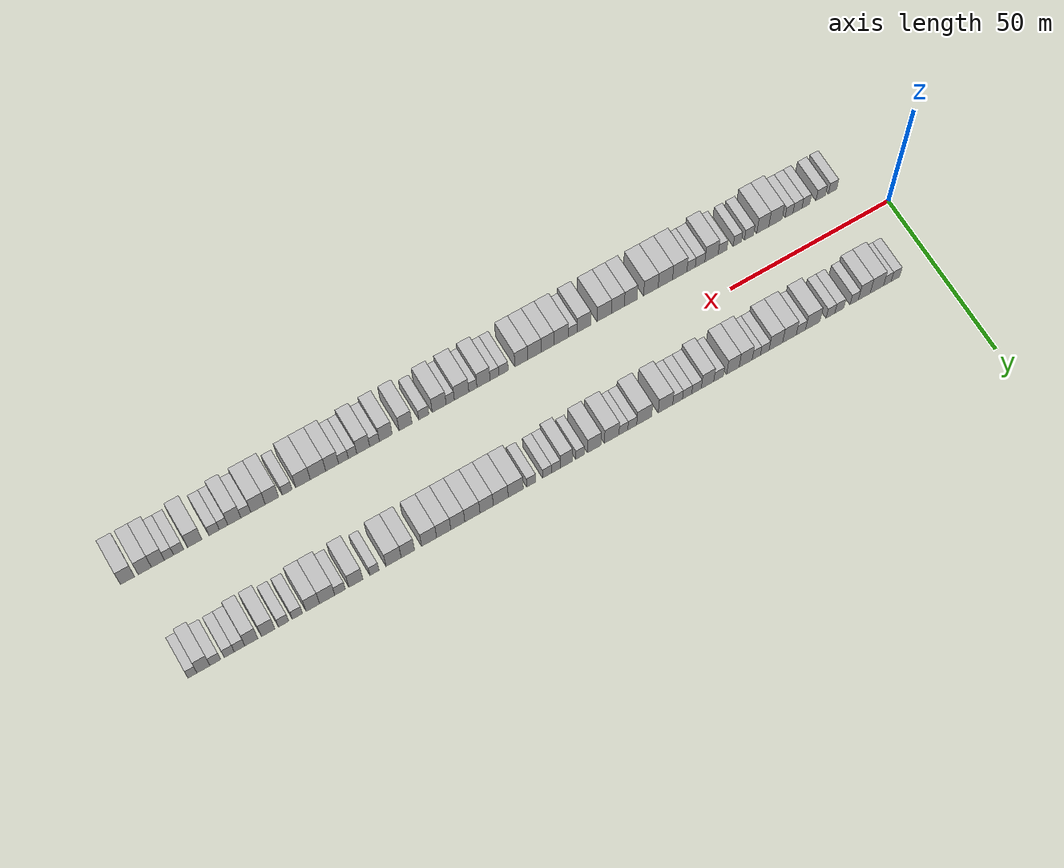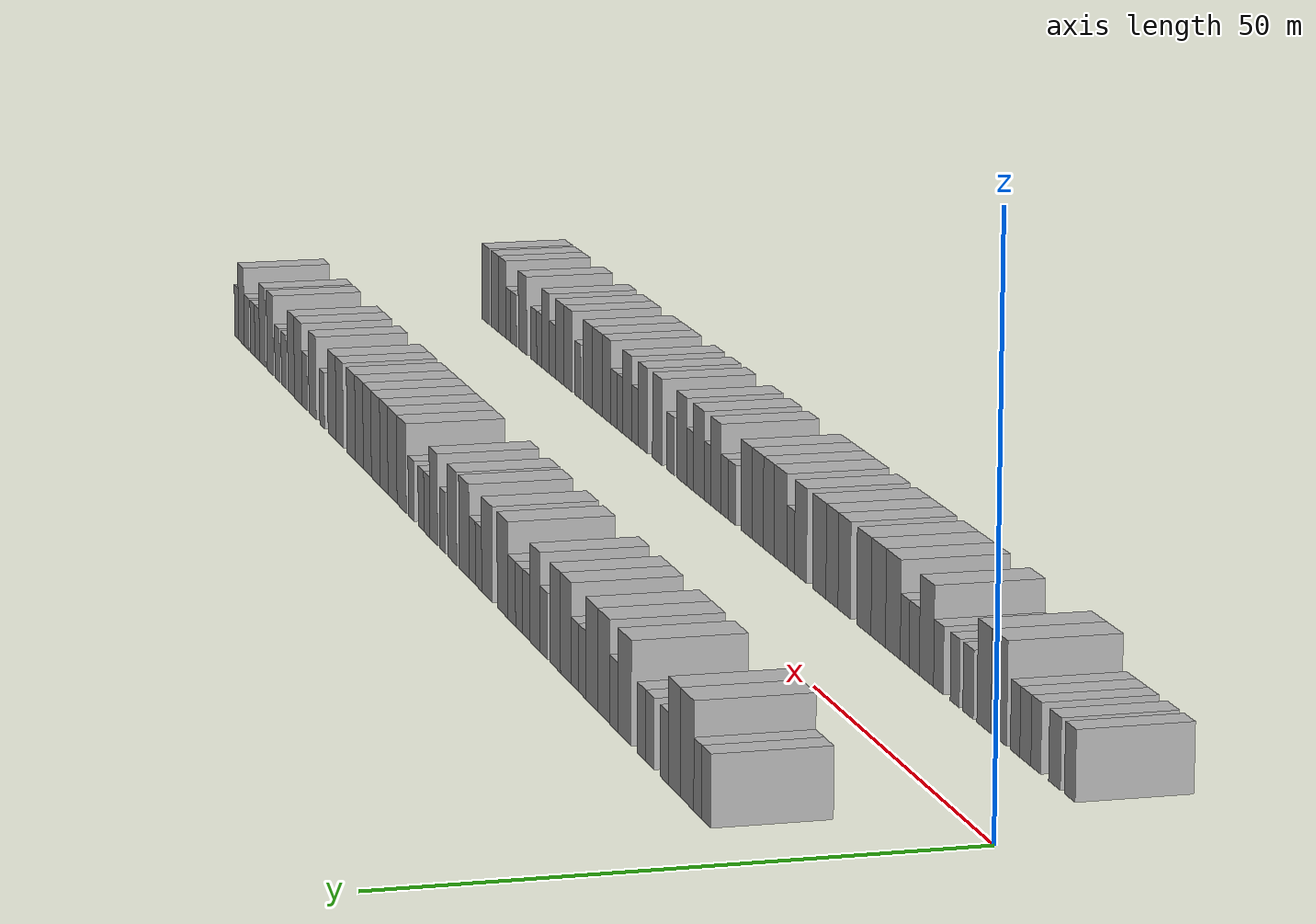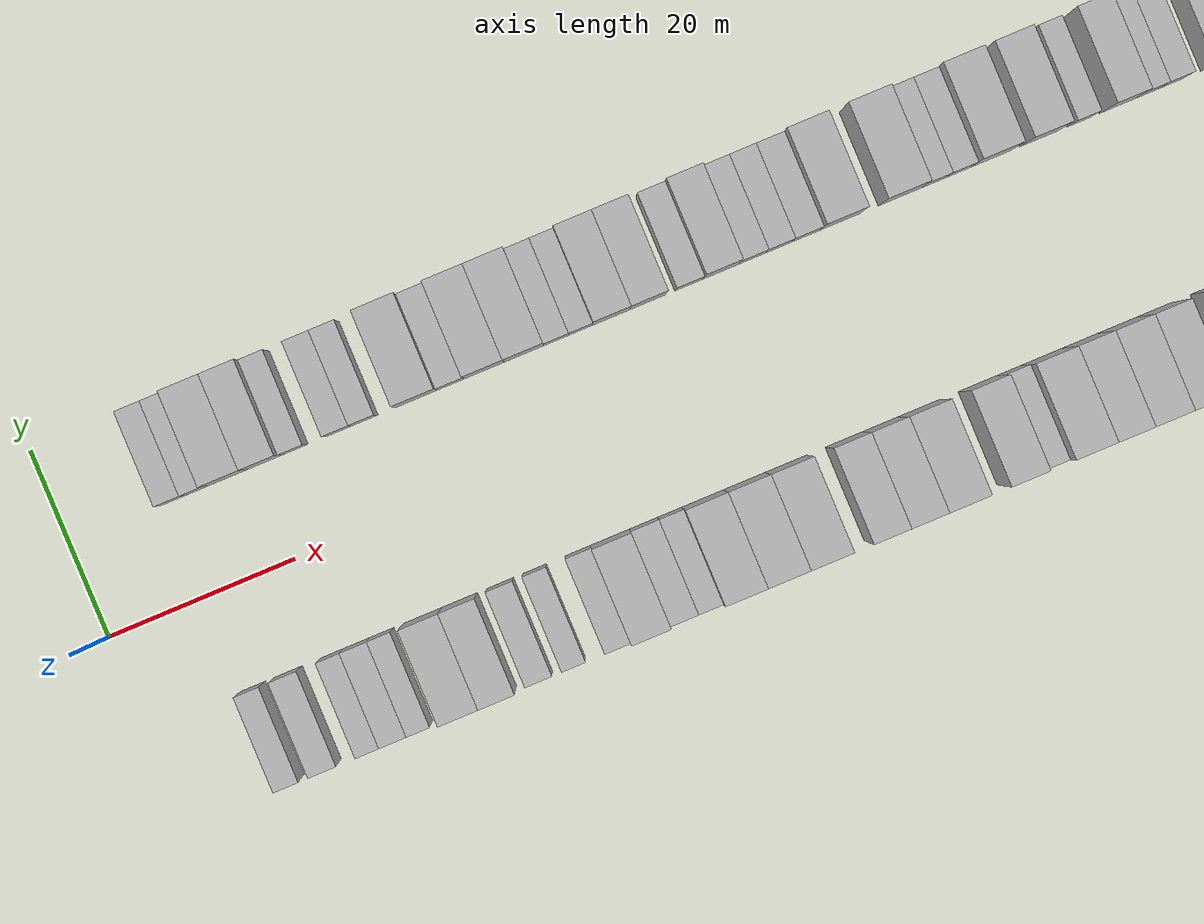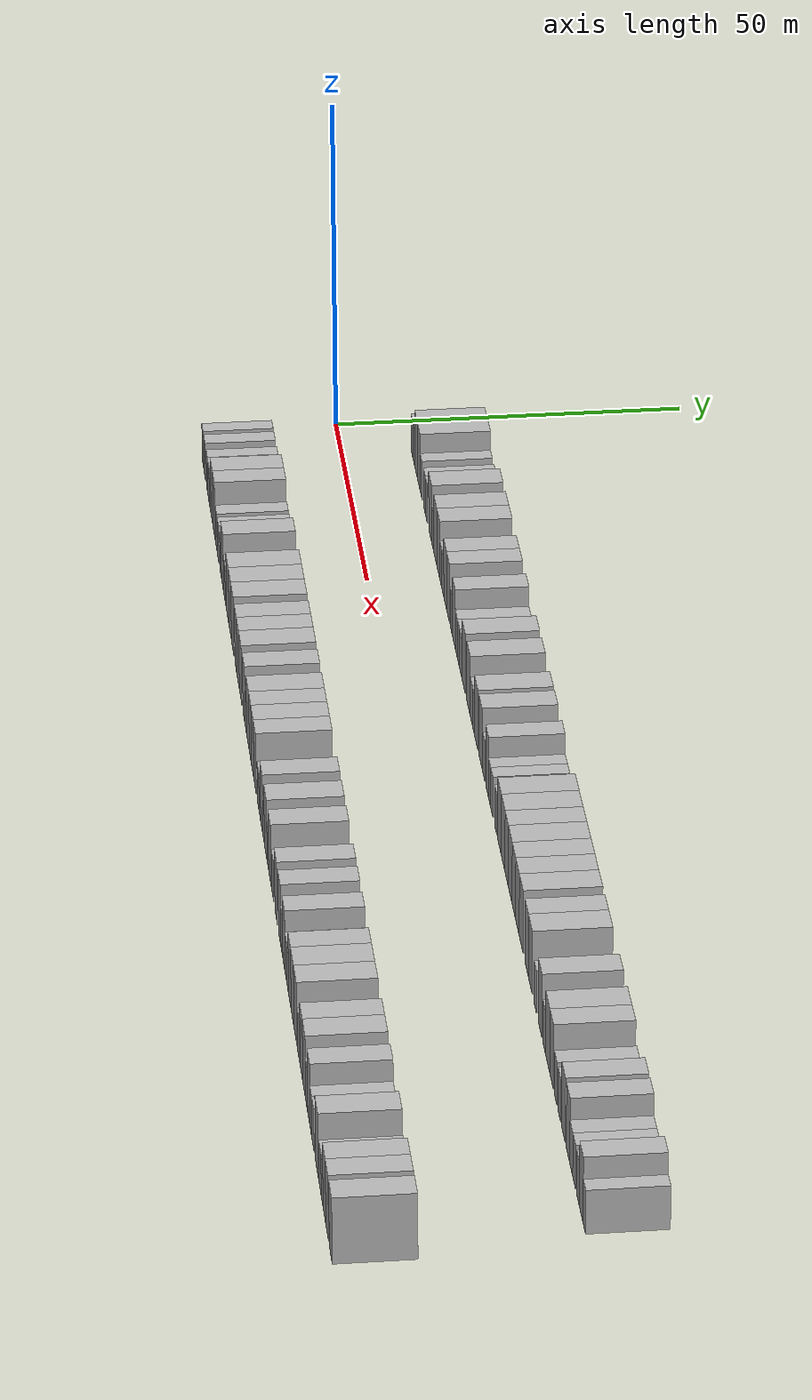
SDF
<sdf version="1.6">
 <world name="default">
  <scene>
   <sky><clouds><speed>12</speed></clouds></sky>
   <ambient>0.4 0.4 0.4 1</ambient>
   <background>0.7 0.7 0.7 1</background>
   <shadows>1</shadows>
  </scene>
  <gravity>0 0 -9.8066</gravity>
  <magnetic_field>6e-06 2.3e-05 -4.2e-05</magnetic_field>
  <physics default="0" name="default_physics" type="ode">
   <ode>
    <solver>
     <type>quick</type>
     <iters>10</iters>
     <sor>1.0</sor>
     <use_dynamic_moi_rescaling>0</use_dynamic_moi_rescaling>
    </solver>
    <constraints>
     <cfm>0</cfm>
     <erp>0.2</erp>
     <contact_max_correcting_vel>100</contact_max_correcting_vel>
     <contact_surface_layer>0.001</contact_surface_layer>
    </constraints>
   </ode>
   <max_step_size>0.004</max_step_size>
   <real_time_factor>1</real_time_factor>
   <real_time_update_rate>250</real_time_update_rate>
  </physics>
  <light name="sun" type="directional">
   <pose>0 0 10 0 0 0</pose>
   <diffuse>0.8 0.8 0.8 1</diffuse>
   <specular>0.2 0.2 0.2 1</specular>
   <attenuation>
    <range>1000</range>
    <constant>0.9</constant>
    <linear>0.01</linear>
    <quadratic>0.001</quadratic>
   </attenuation>
   <direction>-0.5 0.1 -0.9</direction>
  </light>
  <model name="building_1">
   <static>1</static>
   <pose>11.3372 15.0000 0 0.000000 0.000000 1.570796</pose>
   <link name="link">
    <pose>0 0 3.00 0 0 0</pose>
    <collision name="collision"><geometry><box><size>10.0000 2.6744 6.0000</size></box></geometry></collision>
    <visual name="visual">
     <cast_shadows>0</cast_shadows>
     <geometry><box><size>10.0000 2.6744 6.0000</size></box></geometry>
     <material>
      <script>
       <uri>model://HANNAS_wall/materials/scripts</uri>
       <uri>model://HANNAS_wall/materials/textures</uri>
       <name>vrc/HANNAS_wall</name>
      </script>
     </material>
    </visual>
   </link>
  </model>
  <model name="building_2">
   <static>1</static>
   <pose>13.8785 15.0000 0 0.000000 0.000000 1.570796</pose>
   <link name="link">
    <pose>0 0 3.00 0 0 0</pose>
    <collision name="collision"><geometry><box><size>10.0000 2.4080 6.0000</size></box></geometry></collision>
    <visual name="visual">
     <cast_shadows>0</cast_shadows>
     <geometry><box><size>10.0000 2.4080 6.0000</size></box></geometry>
     <material>
      <script>
       <uri>model://HANNAS_wall/materials/scripts</uri>
       <uri>model://HANNAS_wall/materials/textures</uri>
       <name>vrc/HANNAS_wall</name>
      </script>
     </material>
    </visual>
   </link>
  </model>
  <model name="building_3">
   <static>1</static>
   <pose>17.1930 15.0000 0 0.000000 0.000000 1.570796</pose>
   <link name="link">
    <pose>0 0 4.50 0 0 0</pose>
    <collision name="collision"><geometry><box><size>10.0000 4.2211 9.0000</size></box></geometry></collision>
    <visual name="visual">
     <cast_shadows>0</cast_shadows>
     <geometry><box><size>10.0000 4.2211 9.0000</size></box></geometry>
     <material>
      <script>
       <uri>model://HANNAS_wall/materials/scripts</uri>
       <uri>model://HANNAS_wall/materials/textures</uri>
       <name>vrc/HANNAS_wall</name>
      </script>
     </material>
    </visual>
   </link>
  </model>
  <model name="building_4">
   <static>1</static>
   <pose>21.1514 15.0000 0 0.000000 0.000000 1.570796</pose>
   <link name="link">
    <pose>0 0 4.50 0 0 0</pose>
    <collision name="collision"><geometry><box><size>10.0000 3.6958 9.0000</size></box></geometry></collision>
    <visual name="visual">
     <cast_shadows>0</cast_shadows>
     <geometry><box><size>10.0000 3.6958 9.0000</size></box></geometry>
     <material>
      <script>
       <uri>model://HANNAS_wall/materials/scripts</uri>
       <uri>model://HANNAS_wall/materials/textures</uri>
       <name>vrc/HANNAS_wall</name>
      </script>
     </material>
    </visual>
   </link>
  </model>
  <model name="building_5">
   <static>1</static>
   <pose>24.2985 15.0000 0 0.000000 0.000000 1.570796</pose>
   <link name="link">
    <pose>0 0 3.00 0 0 0</pose>
    <collision name="collision"><geometry><box><size>10.0000 2.5983 6.0000</size></box></geometry></collision>
    <visual name="visual">
     <cast_shadows>0</cast_shadows>
     <geometry><box><size>10.0000 2.5983 6.0000</size></box></geometry>
     <material>
      <script>
       <uri>model://HANNAS_wall/materials/scripts</uri>
       <uri>model://HANNAS_wall/materials/textures</uri>
       <name>vrc/HANNAS_wall</name>
      </script>
     </material>
    </visual>
   </link>
  </model>
  <model name="building_6">
   <static>1</static>
   <pose>28.9933 15.0000 0 0.000000 0.000000 1.570796</pose>
   <link name="link">
    <pose>0 0 3.00 0 0 0</pose>
    <collision name="collision"><geometry><box><size>10.0000 2.7913 6.0000</size></box></geometry></collision>
    <visual name="visual">
     <cast_shadows>0</cast_shadows>
     <geometry><box><size>10.0000 2.7913 6.0000</size></box></geometry>
     <material>
      <script>
       <uri>model://HANNAS_wall/materials/scripts</uri>
       <uri>model://HANNAS_wall/materials/textures</uri>
       <name>vrc/HANNAS_wall</name>
      </script>
     </material>
    </visual>
   </link>
  </model>
  <model name="building_7">
   <static>1</static>
   <pose>31.7404 15.0000 0 0.000000 0.000000 1.570796</pose>
   <link name="link">
    <pose>0 0 3.00 0 0 0</pose>
    <collision name="collision"><geometry><box><size>10.0000 2.7030 6.0000</size></box></geometry></collision>
    <visual name="visual">
     <cast_shadows>0</cast_shadows>
     <geometry><box><size>10.0000 2.7030 6.0000</size></box></geometry>
     <material>
      <script>
       <uri>model://HANNAS_wall/materials/scripts</uri>
       <uri>model://HANNAS_wall/materials/textures</uri>
       <name>vrc/HANNAS_wall</name>
      </script>
     </material>
    </visual>
   </link>
  </model>
  <model name="building_8">
   <static>1</static>
   <pose>37.3140 15.0000 0 0.000000 0.000000 1.570796</pose>
   <link name="link">
    <pose>0 0 4.50 0 0 0</pose>
    <collision name="collision"><geometry><box><size>10.0000 4.4440 9.0000</size></box></geometry></collision>
    <visual name="visual">
     <cast_shadows>0</cast_shadows>
     <geometry><box><size>10.0000 4.4440 9.0000</size></box></geometry>
     <material>
      <script>
       <uri>model://HANNAS_wall/materials/scripts</uri>
       <uri>model://HANNAS_wall/materials/textures</uri>
       <name>vrc/HANNAS_wall</name>
      </script>
     </material>
    </visual>
   </link>
  </model>
  <model name="building_9">
   <static>1</static>
   <pose>40.9731 15.0000 0 0.000000 0.000000 1.570796</pose>
   <link name="link">
    <pose>0 0 3.00 0 0 0</pose>
    <collision name="collision"><geometry><box><size>10.0000 2.8742 6.0000</size></box></geometry></collision>
    <visual name="visual">
     <cast_shadows>0</cast_shadows>
     <geometry><box><size>10.0000 2.8742 6.0000</size></box></geometry>
     <material>
      <script>
       <uri>model://HANNAS_wall/materials/scripts</uri>
       <uri>model://HANNAS_wall/materials/textures</uri>
       <name>vrc/HANNAS_wall</name>
      </script>
     </material>
    </visual>
   </link>
  </model>
  <model name="building_10">
   <static>1</static>
   <pose>44.5333 15.0000 0 0.000000 0.000000 1.570796</pose>
   <link name="link">
    <pose>0 0 4.50 0 0 0</pose>
    <collision name="collision"><geometry><box><size>10.0000 4.2464 9.0000</size></box></geometry></collision>
    <visual name="visual">
     <cast_shadows>0</cast_shadows>
     <geometry><box><size>10.0000 4.2464 9.0000</size></box></geometry>
     <material>
      <script>
       <uri>model://HANNAS_wall/materials/scripts</uri>
       <uri>model://HANNAS_wall/materials/textures</uri>
       <name>vrc/HANNAS_wall</name>
      </script>
     </material>
    </visual>
   </link>
  </model>
  <model name="building_11">
   <static>1</static>
   <pose>48.7557 15.0000 0 0.000000 0.000000 1.570796</pose>
   <link name="link">
    <pose>0 0 4.50 0 0 0</pose>
    <collision name="collision"><geometry><box><size>10.0000 4.1984 9.0000</size></box></geometry></collision>
    <visual name="visual">
     <cast_shadows>0</cast_shadows>
     <geometry><box><size>10.0000 4.1984 9.0000</size></box></geometry>
     <material>
      <script>
       <uri>model://HANNAS_wall/materials/scripts</uri>
       <uri>model://HANNAS_wall/materials/textures</uri>
       <name>vrc/HANNAS_wall</name>
      </script>
     </material>
    </visual>
   </link>
  </model>
  <model name="building_12">
   <static>1</static>
   <pose>52.1893 15.0000 0 0.000000 0.000000 1.570796</pose>
   <link name="link">
    <pose>0 0 3.00 0 0 0</pose>
    <collision name="collision"><geometry><box><size>10.0000 2.6688 6.0000</size></box></geometry></collision>
    <visual name="visual">
     <cast_shadows>0</cast_shadows>
     <geometry><box><size>10.0000 2.6688 6.0000</size></box></geometry>
     <material>
      <script>
       <uri>model://HANNAS_wall/materials/scripts</uri>
       <uri>model://HANNAS_wall/materials/textures</uri>
       <name>vrc/HANNAS_wall</name>
      </script>
     </material>
    </visual>
   </link>
  </model>
  <model name="building_13">
   <static>1</static>
   <pose>54.8003 15.0000 0 0.000000 0.000000 1.570796</pose>
   <link name="link">
    <pose>0 0 3.00 0 0 0</pose>
    <collision name="collision"><geometry><box><size>10.0000 2.5532 6.0000</size></box></geometry></collision>
    <visual name="visual">
     <cast_shadows>0</cast_shadows>
     <geometry><box><size>10.0000 2.5532 6.0000</size></box></geometry>
     <material>
      <script>
       <uri>model://HANNAS_wall/materials/scripts</uri>
       <uri>model://HANNAS_wall/materials/textures</uri>
       <name>vrc/HANNAS_wall</name>
      </script>
     </material>
    </visual>
   </link>
  </model>
  <model name="building_14">
   <static>1</static>
   <pose>58.0679 15.0000 0 0.000000 0.000000 1.570796</pose>
   <link name="link">
    <pose>0 0 4.50 0 0 0</pose>
    <collision name="collision"><geometry><box><size>10.0000 3.9819 9.0000</size></box></geometry></collision>
    <visual name="visual">
     <cast_shadows>0</cast_shadows>
     <geometry><box><size>10.0000 3.9819 9.0000</size></box></geometry>
     <material>
      <script>
       <uri>model://HANNAS_wall/materials/scripts</uri>
       <uri>model://HANNAS_wall/materials/textures</uri>
       <name>vrc/HANNAS_wall</name>
      </script>
     </material>
    </visual>
   </link>
  </model>
  <model name="building_15">
   <static>1</static>
   <pose>61.9804 15.0000 0 0.000000 0.000000 1.570796</pose>
   <link name="link">
    <pose>0 0 4.50 0 0 0</pose>
    <collision name="collision"><geometry><box><size>10.0000 3.8432 9.0000</size></box></geometry></collision>
    <visual name="visual">
     <cast_shadows>0</cast_shadows>
     <geometry><box><size>10.0000 3.8432 9.0000</size></box></geometry>
     <material>
      <script>
       <uri>model://HANNAS_wall/materials/scripts</uri>
       <uri>model://HANNAS_wall/materials/textures</uri>
       <name>vrc/HANNAS_wall</name>
      </script>
     </material>
    </visual>
   </link>
  </model>
  <model name="building_16">
   <static>1</static>
   <pose>66.3748 15.0000 0 0.000000 0.000000 1.570796</pose>
   <link name="link">
    <pose>0 0 3.00 0 0 0</pose>
    <collision name="collision"><geometry><box><size>10.0000 2.9455 6.0000</size></box></geometry></collision>
    <visual name="visual">
     <cast_shadows>0</cast_shadows>
     <geometry><box><size>10.0000 2.9455 6.0000</size></box></geometry>
     <material>
      <script>
       <uri>model://HANNAS_wall/materials/scripts</uri>
       <uri>model://HANNAS_wall/materials/textures</uri>
       <name>vrc/HANNAS_wall</name>
      </script>
     </material>
    </visual>
   </link>
  </model>
  <model name="building_17">
   <static>1</static>
   <pose>69.7596 15.0000 0 0.000000 0.000000 1.570796</pose>
   <link name="link">
    <pose>0 0 4.50 0 0 0</pose>
    <collision name="collision"><geometry><box><size>10.0000 3.8243 9.0000</size></box></geometry></collision>
    <visual name="visual">
     <cast_shadows>0</cast_shadows>
     <geometry><box><size>10.0000 3.8243 9.0000</size></box></geometry>
     <material>
      <script>
       <uri>model://HANNAS_wall/materials/scripts</uri>
       <uri>model://HANNAS_wall/materials/textures</uri>
       <name>vrc/HANNAS_wall</name>
      </script>
     </material>
    </visual>
   </link>
  </model>
  <model name="building_18">
   <static>1</static>
   <pose>73.1181 15.0000 0 0.000000 0.000000 1.570796</pose>
   <link name="link">
    <pose>0 0 3.00 0 0 0</pose>
    <collision name="collision"><geometry><box><size>10.0000 2.8927 6.0000</size></box></geometry></collision>
    <visual name="visual">
     <cast_shadows>0</cast_shadows>
     <geometry><box><size>10.0000 2.8927 6.0000</size></box></geometry>
     <material>
      <script>
       <uri>model://HANNAS_wall/materials/scripts</uri>
       <uri>model://HANNAS_wall/materials/textures</uri>
       <name>vrc/HANNAS_wall</name>
      </script>
     </material>
    </visual>
   </link>
  </model>
  <model name="building_19">
   <static>1</static>
   <pose>75.9669 15.0000 0 0.000000 0.000000 1.570796</pose>
   <link name="link">
    <pose>0 0 3.00 0 0 0</pose>
    <collision name="collision"><geometry><box><size>10.0000 2.8049 6.0000</size></box></geometry></collision>
    <visual name="visual">
     <cast_shadows>0</cast_shadows>
     <geometry><box><size>10.0000 2.8049 6.0000</size></box></geometry>
     <material>
      <script>
       <uri>model://HANNAS_wall/materials/scripts</uri>
       <uri>model://HANNAS_wall/materials/textures</uri>
       <name>vrc/HANNAS_wall</name>
      </script>
     </material>
    </visual>
   </link>
  </model>
  <model name="building_20">
   <static>1</static>
   <pose>78.8637 15.0000 0 0.000000 0.000000 1.570796</pose>
   <link name="link">
    <pose>0 0 3.00 0 0 0</pose>
    <collision name="collision"><geometry><box><size>10.0000 2.9887 6.0000</size></box></geometry></collision>
    <visual name="visual">
     <cast_shadows>0</cast_shadows>
     <geometry><box><size>10.0000 2.9887 6.0000</size></box></geometry>
     <material>
      <script>
       <uri>model://HANNAS_wall/materials/scripts</uri>
       <uri>model://HANNAS_wall/materials/textures</uri>
       <name>vrc/HANNAS_wall</name>
      </script>
     </material>
    </visual>
   </link>
  </model>
  <model name="building_21">
   <static>1</static>
   <pose>82.5431 15.0000 0 0.000000 0.000000 1.570796</pose>
   <link name="link">
    <pose>0 0 4.50 0 0 0</pose>
    <collision name="collision"><geometry><box><size>10.0000 4.3702 9.0000</size></box></geometry></collision>
    <visual name="visual">
     <cast_shadows>0</cast_shadows>
     <geometry><box><size>10.0000 4.3702 9.0000</size></box></geometry>
     <material>
      <script>
       <uri>model://HANNAS_wall/materials/scripts</uri>
       <uri>model://HANNAS_wall/materials/textures</uri>
       <name>vrc/HANNAS_wall</name>
      </script>
     </material>
    </visual>
   </link>
  </model>
  <model name="building_22">
   <static>1</static>
   <pose>88.9695 15.0000 0 0.000000 0.000000 1.570796</pose>
   <link name="link">
    <pose>0 0 4.50 0 0 0</pose>
    <collision name="collision"><geometry><box><size>10.0000 4.4826 9.0000</size></box></geometry></collision>
    <visual name="visual">
     <cast_shadows>0</cast_shadows>
     <geometry><box><size>10.0000 4.4826 9.0000</size></box></geometry>
     <material>
      <script>
       <uri>model://HANNAS_wall/materials/scripts</uri>
       <uri>model://HANNAS_wall/materials/textures</uri>
       <name>vrc/HANNAS_wall</name>
      </script>
     </material>
    </visual>
   </link>
  </model>
  <model name="building_23">
   <static>1</static>
   <pose>92.5445 15.0000 0 0.000000 0.000000 1.570796</pose>
   <link name="link">
    <pose>0 0 3.00 0 0 0</pose>
    <collision name="collision"><geometry><box><size>10.0000 2.6674 6.0000</size></box></geometry></collision>
    <visual name="visual">
     <cast_shadows>0</cast_shadows>
     <geometry><box><size>10.0000 2.6674 6.0000</size></box></geometry>
     <material>
      <script>
       <uri>model://HANNAS_wall/materials/scripts</uri>
       <uri>model://HANNAS_wall/materials/textures</uri>
       <name>vrc/HANNAS_wall</name>
      </script>
     </material>
    </visual>
   </link>
  </model>
  <model name="building_24">
   <static>1</static>
   <pose>95.2123 15.0000 0 0.000000 0.000000 1.570796</pose>
   <link name="link">
    <pose>0 0 3.00 0 0 0</pose>
    <collision name="collision"><geometry><box><size>10.0000 2.6682 6.0000</size></box></geometry></collision>
    <visual name="visual">
     <cast_shadows>0</cast_shadows>
     <geometry><box><size>10.0000 2.6682 6.0000</size></box></geometry>
     <material>
      <script>
       <uri>model://HANNAS_wall/materials/scripts</uri>
       <uri>model://HANNAS_wall/materials/textures</uri>
       <name>vrc/HANNAS_wall</name>
      </script>
     </material>
    </visual>
   </link>
  </model>
  <model name="building_25">
   <static>1</static>
   <pose>98.7237 15.0000 0 0.000000 0.000000 1.570796</pose>
   <link name="link">
    <pose>0 0 4.50 0 0 0</pose>
    <collision name="collision"><geometry><box><size>10.0000 4.3547 9.0000</size></box></geometry></collision>
    <visual name="visual">
     <cast_shadows>0</cast_shadows>
     <geometry><box><size>10.0000 4.3547 9.0000</size></box></geometry>
     <material>
      <script>
       <uri>model://HANNAS_wall/materials/scripts</uri>
       <uri>model://HANNAS_wall/materials/textures</uri>
       <name>vrc/HANNAS_wall</name>
      </script>
     </material>
    </visual>
   </link>
  </model>
  <model name="building_26">
   <static>1</static>
   <pose>103.9300 15.0000 0 0.000000 0.000000 1.570796</pose>
   <link name="link">
    <pose>0 0 4.50 0 0 0</pose>
    <collision name="collision"><geometry><box><size>10.0000 4.0577 9.0000</size></box></geometry></collision>
    <visual name="visual">
     <cast_shadows>0</cast_shadows>
     <geometry><box><size>10.0000 4.0577 9.0000</size></box></geometry>
     <material>
      <script>
       <uri>model://HANNAS_wall/materials/scripts</uri>
       <uri>model://HANNAS_wall/materials/textures</uri>
       <name>vrc/HANNAS_wall</name>
      </script>
     </material>
    </visual>
   </link>
  </model>
  <model name="building_27">
   <static>1</static>
   <pose>108.2009 15.0000 0 0.000000 0.000000 1.570796</pose>
   <link name="link">
    <pose>0 0 3.00 0 0 0</pose>
    <collision name="collision"><geometry><box><size>10.0000 2.4841 6.0000</size></box></geometry></collision>
    <visual name="visual">
     <cast_shadows>0</cast_shadows>
     <geometry><box><size>10.0000 2.4841 6.0000</size></box></geometry>
     <material>
      <script>
       <uri>model://HANNAS_wall/materials/scripts</uri>
       <uri>model://HANNAS_wall/materials/textures</uri>
       <name>vrc/HANNAS_wall</name>
      </script>
     </material>
    </visual>
   </link>
  </model>
  <model name="building_28">
   <static>1</static>
   <pose>112.2435 15.0000 0 0.000000 0.000000 1.570796</pose>
   <link name="link">
    <pose>0 0 4.50 0 0 0</pose>
    <collision name="collision"><geometry><box><size>10.0000 3.6010 9.0000</size></box></geometry></collision>
    <visual name="visual">
     <cast_shadows>0</cast_shadows>
     <geometry><box><size>10.0000 3.6010 9.0000</size></box></geometry>
     <material>
      <script>
       <uri>model://HANNAS_wall/materials/scripts</uri>
       <uri>model://HANNAS_wall/materials/textures</uri>
       <name>vrc/HANNAS_wall</name>
      </script>
     </material>
    </visual>
   </link>
  </model>
  <model name="building_29">
   <static>1</static>
   <pose>115.3490 15.0000 0 0.000000 0.000000 1.570796</pose>
   <link name="link">
    <pose>0 0 3.00 0 0 0</pose>
    <collision name="collision"><geometry><box><size>10.0000 2.6100 6.0000</size></box></geometry></collision>
    <visual name="visual">
     <cast_shadows>0</cast_shadows>
     <geometry><box><size>10.0000 2.6100 6.0000</size></box></geometry>
     <material>
      <script>
       <uri>model://HANNAS_wall/materials/scripts</uri>
       <uri>model://HANNAS_wall/materials/textures</uri>
       <name>vrc/HANNAS_wall</name>
      </script>
     </material>
    </visual>
   </link>
  </model>
  <model name="building_30">
   <static>1</static>
   <pose>117.9736 15.0000 0 0.000000 0.000000 1.570796</pose>
   <link name="link">
    <pose>0 0 3.00 0 0 0</pose>
    <collision name="collision"><geometry><box><size>10.0000 2.6391 6.0000</size></box></geometry></collision>
    <visual name="visual">
     <cast_shadows>0</cast_shadows>
     <geometry><box><size>10.0000 2.6391 6.0000</size></box></geometry>
     <material>
      <script>
       <uri>model://HANNAS_wall/materials/scripts</uri>
       <uri>model://HANNAS_wall/materials/textures</uri>
       <name>vrc/HANNAS_wall</name>
      </script>
     </material>
    </visual>
   </link>
  </model>
  <model name="building_31">
   <static>1</static>
   <pose>122.6440 15.0000 0 0.000000 0.000000 1.570796</pose>
   <link name="link">
    <pose>0 0 3.00 0 0 0</pose>
    <collision name="collision"><geometry><box><size>10.0000 2.7017 6.0000</size></box></geometry></collision>
    <visual name="visual">
     <cast_shadows>0</cast_shadows>
     <geometry><box><size>10.0000 2.7017 6.0000</size></box></geometry>
     <material>
      <script>
       <uri>model://HANNAS_wall/materials/scripts</uri>
       <uri>model://HANNAS_wall/materials/textures</uri>
       <name>vrc/HANNAS_wall</name>
      </script>
     </material>
    </visual>
   </link>
  </model>
  <model name="building_32">
   <static>1</static>
   <pose>127.2096 15.0000 0 0.000000 0.000000 1.570796</pose>
   <link name="link">
    <pose>0 0 4.50 0 0 0</pose>
    <collision name="collision"><geometry><box><size>10.0000 4.4295 9.0000</size></box></geometry></collision>
    <visual name="visual">
     <cast_shadows>0</cast_shadows>
     <geometry><box><size>10.0000 4.4295 9.0000</size></box></geometry>
     <material>
      <script>
       <uri>model://HANNAS_wall/materials/scripts</uri>
       <uri>model://HANNAS_wall/materials/textures</uri>
       <name>vrc/HANNAS_wall</name>
      </script>
     </material>
    </visual>
   </link>
  </model>
  <model name="building_33">
   <static>1</static>
   <pose>131.6204 15.0000 0 0.000000 0.000000 1.570796</pose>
   <link name="link">
    <pose>0 0 4.50 0 0 0</pose>
    <collision name="collision"><geometry><box><size>10.0000 4.3922 9.0000</size></box></geometry></collision>
    <visual name="visual">
     <cast_shadows>0</cast_shadows>
     <geometry><box><size>10.0000 4.3922 9.0000</size></box></geometry>
     <material>
      <script>
       <uri>model://HANNAS_wall/materials/scripts</uri>
       <uri>model://HANNAS_wall/materials/textures</uri>
       <name>vrc/HANNAS_wall</name>
      </script>
     </material>
    </visual>
   </link>
  </model>
  <model name="building_34">
   <static>1</static>
   <pose>135.7566 15.0000 0 0.000000 0.000000 1.570796</pose>
   <link name="link">
    <pose>0 0 4.50 0 0 0</pose>
    <collision name="collision"><geometry><box><size>10.0000 3.8801 9.0000</size></box></geometry></collision>
    <visual name="visual">
     <cast_shadows>0</cast_shadows>
     <geometry><box><size>10.0000 3.8801 9.0000</size></box></geometry>
     <material>
      <script>
       <uri>model://HANNAS_wall/materials/scripts</uri>
       <uri>model://HANNAS_wall/materials/textures</uri>
       <name>vrc/HANNAS_wall</name>
      </script>
     </material>
    </visual>
   </link>
  </model>
  <model name="building_35">
   <static>1</static>
   <pose>139.9109 15.0000 0 0.000000 0.000000 1.570796</pose>
   <link name="link">
    <pose>0 0 4.50 0 0 0</pose>
    <collision name="collision"><geometry><box><size>10.0000 4.4286 9.0000</size></box></geometry></collision>
    <visual name="visual">
     <cast_shadows>0</cast_shadows>
     <geometry><box><size>10.0000 4.4286 9.0000</size></box></geometry>
     <material>
      <script>
       <uri>model://HANNAS_wall/materials/scripts</uri>
       <uri>model://HANNAS_wall/materials/textures</uri>
       <name>vrc/HANNAS_wall</name>
      </script>
     </material>
    </visual>
   </link>
  </model>
  <model name="building_36">
   <static>1</static>
   <pose>144.1624 15.0000 0 0.000000 0.000000 1.570796</pose>
   <link name="link">
    <pose>0 0 4.50 0 0 0</pose>
    <collision name="collision"><geometry><box><size>10.0000 4.0744 9.0000</size></box></geometry></collision>
    <visual name="visual">
     <cast_shadows>0</cast_shadows>
     <geometry><box><size>10.0000 4.0744 9.0000</size></box></geometry>
     <material>
      <script>
       <uri>model://HANNAS_wall/materials/scripts</uri>
       <uri>model://HANNAS_wall/materials/textures</uri>
       <name>vrc/HANNAS_wall</name>
      </script>
     </material>
    </visual>
   </link>
  </model>
  <model name="building_37">
   <static>1</static>
   <pose>148.2636 15.0000 0 0.000000 0.000000 1.570796</pose>
   <link name="link">
    <pose>0 0 4.50 0 0 0</pose>
    <collision name="collision"><geometry><box><size>10.0000 4.1281 9.0000</size></box></geometry></collision>
    <visual name="visual">
     <cast_shadows>0</cast_shadows>
     <geometry><box><size>10.0000 4.1281 9.0000</size></box></geometry>
     <material>
      <script>
       <uri>model://HANNAS_wall/materials/scripts</uri>
       <uri>model://HANNAS_wall/materials/textures</uri>
       <name>vrc/HANNAS_wall</name>
      </script>
     </material>
    </visual>
   </link>
  </model>
  <model name="building_38">
   <static>1</static>
   <pose>152.5058 15.0000 0 0.000000 0.000000 1.570796</pose>
   <link name="link">
    <pose>0 0 4.50 0 0 0</pose>
    <collision name="collision"><geometry><box><size>10.0000 4.3564 9.0000</size></box></geometry></collision>
    <visual name="visual">
     <cast_shadows>0</cast_shadows>
     <geometry><box><size>10.0000 4.3564 9.0000</size></box></geometry>
     <material>
      <script>
       <uri>model://HANNAS_wall/materials/scripts</uri>
       <uri>model://HANNAS_wall/materials/textures</uri>
       <name>vrc/HANNAS_wall</name>
      </script>
     </material>
    </visual>
   </link>
  </model>
  <model name="building_39">
   <static>1</static>
   <pose>158.6110 15.0000 0 0.000000 0.000000 1.570796</pose>
   <link name="link">
    <pose>0 0 4.50 0 0 0</pose>
    <collision name="collision"><geometry><box><size>10.0000 3.8540 9.0000</size></box></geometry></collision>
    <visual name="visual">
     <cast_shadows>0</cast_shadows>
     <geometry><box><size>10.0000 3.8540 9.0000</size></box></geometry>
     <material>
      <script>
       <uri>model://HANNAS_wall/materials/scripts</uri>
       <uri>model://HANNAS_wall/materials/textures</uri>
       <name>vrc/HANNAS_wall</name>
      </script>
     </material>
    </visual>
   </link>
  </model>
  <model name="building_40">
   <static>1</static>
   <pose>162.7305 15.0000 0 0.000000 0.000000 1.570796</pose>
   <link name="link">
    <pose>0 0 4.50 0 0 0</pose>
    <collision name="collision"><geometry><box><size>10.0000 4.3849 9.0000</size></box></geometry></collision>
    <visual name="visual">
     <cast_shadows>0</cast_shadows>
     <geometry><box><size>10.0000 4.3849 9.0000</size></box></geometry>
     <material>
      <script>
       <uri>model://HANNAS_wall/materials/scripts</uri>
       <uri>model://HANNAS_wall/materials/textures</uri>
       <name>vrc/HANNAS_wall</name>
      </script>
     </material>
    </visual>
   </link>
  </model>
  <model name="building_41">
   <static>1</static>
   <pose>168.2287 15.0000 0 0.000000 0.000000 1.570796</pose>
   <link name="link">
    <pose>0 0 3.00 0 0 0</pose>
    <collision name="collision"><geometry><box><size>10.0000 2.6116 6.0000</size></box></geometry></collision>
    <visual name="visual">
     <cast_shadows>0</cast_shadows>
     <geometry><box><size>10.0000 2.6116 6.0000</size></box></geometry>
     <material>
      <script>
       <uri>model://HANNAS_wall/materials/scripts</uri>
       <uri>model://HANNAS_wall/materials/textures</uri>
       <name>vrc/HANNAS_wall</name>
      </script>
     </material>
    </visual>
   </link>
  </model>
  <model name="building_42">
   <static>1</static>
   <pose>173.5379 15.0000 0 0.000000 0.000000 1.570796</pose>
   <link name="link">
    <pose>0 0 4.50 0 0 0</pose>
    <collision name="collision"><geometry><box><size>10.0000 4.0069 9.0000</size></box></geometry></collision>
    <visual name="visual">
     <cast_shadows>0</cast_shadows>
     <geometry><box><size>10.0000 4.0069 9.0000</size></box></geometry>
     <material>
      <script>
       <uri>model://HANNAS_wall/materials/scripts</uri>
       <uri>model://HANNAS_wall/materials/textures</uri>
       <name>vrc/HANNAS_wall</name>
      </script>
     </material>
    </visual>
   </link>
  </model>
  <model name="building_43">
   <static>1</static>
   <pose>178.0352 15.0000 0 0.000000 0.000000 1.570796</pose>
   <link name="link">
    <pose>0 0 3.00 0 0 0</pose>
    <collision name="collision"><geometry><box><size>10.0000 2.9876 6.0000</size></box></geometry></collision>
    <visual name="visual">
     <cast_shadows>0</cast_shadows>
     <geometry><box><size>10.0000 2.9876 6.0000</size></box></geometry>
     <material>
      <script>
       <uri>model://HANNAS_wall/materials/scripts</uri>
       <uri>model://HANNAS_wall/materials/textures</uri>
       <name>vrc/HANNAS_wall</name>
      </script>
     </material>
    </visual>
   </link>
  </model>
  <model name="building_44">
   <static>1</static>
   <pose>181.6978 15.0000 0 0.000000 0.000000 1.570796</pose>
   <link name="link">
    <pose>0 0 4.50 0 0 0</pose>
    <collision name="collision"><geometry><box><size>10.0000 4.3375 9.0000</size></box></geometry></collision>
    <visual name="visual">
     <cast_shadows>0</cast_shadows>
     <geometry><box><size>10.0000 4.3375 9.0000</size></box></geometry>
     <material>
      <script>
       <uri>model://HANNAS_wall/materials/scripts</uri>
       <uri>model://HANNAS_wall/materials/textures</uri>
       <name>vrc/HANNAS_wall</name>
      </script>
     </material>
    </visual>
   </link>
  </model>
  <model name="building_45">
   <static>1</static>
   <pose>185.7727 15.0000 0 0.000000 0.000000 1.570796</pose>
   <link name="link">
    <pose>0 0 4.50 0 0 0</pose>
    <collision name="collision"><geometry><box><size>10.0000 3.8123 9.0000</size></box></geometry></collision>
    <visual name="visual">
     <cast_shadows>0</cast_shadows>
     <geometry><box><size>10.0000 3.8123 9.0000</size></box></geometry>
     <material>
      <script>
       <uri>model://HANNAS_wall/materials/scripts</uri>
       <uri>model://HANNAS_wall/materials/textures</uri>
       <name>vrc/HANNAS_wall</name>
      </script>
     </material>
    </visual>
   </link>
  </model>
  <model name="building_46">
   <static>1</static>
   <pose>190.1323 15.0000 0 0.000000 0.000000 1.570796</pose>
   <link name="link">
    <pose>0 0 3.00 0 0 0</pose>
    <collision name="collision"><geometry><box><size>10.0000 2.9071 6.0000</size></box></geometry></collision>
    <visual name="visual">
     <cast_shadows>0</cast_shadows>
     <geometry><box><size>10.0000 2.9071 6.0000</size></box></geometry>
     <material>
      <script>
       <uri>model://HANNAS_wall/materials/scripts</uri>
       <uri>model://HANNAS_wall/materials/textures</uri>
       <name>vrc/HANNAS_wall</name>
      </script>
     </material>
    </visual>
   </link>
  </model>
  <model name="building_47">
   <static>1</static>
   <pose>194.0293 15.0000 0 0.000000 0.000000 1.570796</pose>
   <link name="link">
    <pose>0 0 3.00 0 0 0</pose>
    <collision name="collision"><geometry><box><size>10.0000 2.8869 6.0000</size></box></geometry></collision>
    <visual name="visual">
     <cast_shadows>0</cast_shadows>
     <geometry><box><size>10.0000 2.8869 6.0000</size></box></geometry>
     <material>
      <script>
       <uri>model://HANNAS_wall/materials/scripts</uri>
       <uri>model://HANNAS_wall/materials/textures</uri>
       <name>vrc/HANNAS_wall</name>
      </script>
     </material>
    </visual>
   </link>
  </model>
  <model name="building_48">
   <static>1</static>
   <pose>198.3631 15.0000 0 0.000000 0.000000 1.570796</pose>
   <link name="link">
    <pose>0 0 4.50 0 0 0</pose>
    <collision name="collision"><geometry><box><size>10.0000 3.7808 9.0000</size></box></geometry></collision>
    <visual name="visual">
     <cast_shadows>0</cast_shadows>
     <geometry><box><size>10.0000 3.7808 9.0000</size></box></geometry>
     <material>
      <script>
       <uri>model://HANNAS_wall/materials/scripts</uri>
       <uri>model://HANNAS_wall/materials/textures</uri>
       <name>vrc/HANNAS_wall</name>
      </script>
     </material>
    </visual>
   </link>
  </model>
  <model name="building_49">
   <static>1</static>
   <pose>203.0721 15.0000 0 0.000000 0.000000 1.570796</pose>
   <link name="link">
    <pose>0 0 4.50 0 0 0</pose>
    <collision name="collision"><geometry><box><size>10.0000 3.6371 9.0000</size></box></geometry></collision>
    <visual name="visual">
     <cast_shadows>0</cast_shadows>
     <geometry><box><size>10.0000 3.6371 9.0000</size></box></geometry>
     <material>
      <script>
       <uri>model://HANNAS_wall/materials/scripts</uri>
       <uri>model://HANNAS_wall/materials/textures</uri>
       <name>vrc/HANNAS_wall</name>
      </script>
     </material>
    </visual>
   </link>
  </model>
  <model name="building_50">
   <static>1</static>
   <pose>206.3666 15.0000 0 0.000000 0.000000 1.570796</pose>
   <link name="link">
    <pose>0 0 3.00 0 0 0</pose>
    <collision name="collision"><geometry><box><size>10.0000 2.9518 6.0000</size></box></geometry></collision>
    <visual name="visual">
     <cast_shadows>0</cast_shadows>
     <geometry><box><size>10.0000 2.9518 6.0000</size></box></geometry>
     <material>
      <script>
       <uri>model://HANNAS_wall/materials/scripts</uri>
       <uri>model://HANNAS_wall/materials/textures</uri>
       <name>vrc/HANNAS_wall</name>
      </script>
     </material>
    </visual>
   </link>
  </model>
  <model name="building_51">
   <static>1</static>
   <pose>209.2433 15.0000 0 0.000000 0.000000 1.570796</pose>
   <link name="link">
    <pose>0 0 3.00 0 0 0</pose>
    <collision name="collision"><geometry><box><size>10.0000 2.8016 6.0000</size></box></geometry></collision>
    <visual name="visual">
     <cast_shadows>0</cast_shadows>
     <geometry><box><size>10.0000 2.8016 6.0000</size></box></geometry>
     <material>
      <script>
       <uri>model://HANNAS_wall/materials/scripts</uri>
       <uri>model://HANNAS_wall/materials/textures</uri>
       <name>vrc/HANNAS_wall</name>
      </script>
     </material>
    </visual>
   </link>
  </model>
  <model name="building_52">
   <static>1</static>
   <pose>213.1248 15.0000 0 0.000000 0.000000 1.570796</pose>
   <link name="link">
    <pose>0 0 3.00 0 0 0</pose>
    <collision name="collision"><geometry><box><size>10.0000 2.9612 6.0000</size></box></geometry></collision>
    <visual name="visual">
     <cast_shadows>0</cast_shadows>
     <geometry><box><size>10.0000 2.9612 6.0000</size></box></geometry>
     <material>
      <script>
       <uri>model://HANNAS_wall/materials/scripts</uri>
       <uri>model://HANNAS_wall/materials/textures</uri>
       <name>vrc/HANNAS_wall</name>
      </script>
     </material>
    </visual>
   </link>
  </model>
  <model name="building_53">
   <static>1</static>
   <pose>216.4179 15.0000 0 0.000000 0.000000 1.570796</pose>
   <link name="link">
    <pose>0 0 4.50 0 0 0</pose>
    <collision name="collision"><geometry><box><size>10.0000 3.6251 9.0000</size></box></geometry></collision>
    <visual name="visual">
     <cast_shadows>0</cast_shadows>
     <geometry><box><size>10.0000 3.6251 9.0000</size></box></geometry>
     <material>
      <script>
       <uri>model://HANNAS_wall/materials/scripts</uri>
       <uri>model://HANNAS_wall/materials/textures</uri>
       <name>vrc/HANNAS_wall</name>
      </script>
     </material>
    </visual>
   </link>
  </model>
  <model name="building_54">
   <static>1</static>
   <pose>219.4808 15.0000 0 0.000000 0.000000 1.570796</pose>
   <link name="link">
    <pose>0 0 3.00 0 0 0</pose>
    <collision name="collision"><geometry><box><size>10.0000 2.5008 6.0000</size></box></geometry></collision>
    <visual name="visual">
     <cast_shadows>0</cast_shadows>
     <geometry><box><size>10.0000 2.5008 6.0000</size></box></geometry>
     <material>
      <script>
       <uri>model://HANNAS_wall/materials/scripts</uri>
       <uri>model://HANNAS_wall/materials/textures</uri>
       <name>vrc/HANNAS_wall</name>
      </script>
     </material>
    </visual>
   </link>
  </model>
  <model name="building_55">
   <static>1</static>
   <pose>11.3231 -15.0000 0 0.000000 0.000000 1.570796</pose>
   <link name="link">
    <pose>0 0 3.00 0 0 0</pose>
    <collision name="collision"><geometry><box><size>10.0000 2.6463 6.0000</size></box></geometry></collision>
    <visual name="visual">
     <cast_shadows>0</cast_shadows>
     <geometry><box><size>10.0000 2.6463 6.0000</size></box></geometry>
     <material>
      <script>
       <uri>model://HANNAS_wall/materials/scripts</uri>
       <uri>model://HANNAS_wall/materials/textures</uri>
       <name>vrc/HANNAS_wall</name>
      </script>
     </material>
    </visual>
   </link>
  </model>
  <model name="building_56">
   <static>1</static>
   <pose>15.1235 -15.0000 0 0.000000 0.000000 1.570796</pose>
   <link name="link">
    <pose>0 0 3.00 0 0 0</pose>
    <collision name="collision"><geometry><box><size>10.0000 2.9545 6.0000</size></box></geometry></collision>
    <visual name="visual">
     <cast_shadows>0</cast_shadows>
     <geometry><box><size>10.0000 2.9545 6.0000</size></box></geometry>
     <material>
      <script>
       <uri>model://HANNAS_wall/materials/scripts</uri>
       <uri>model://HANNAS_wall/materials/textures</uri>
       <name>vrc/HANNAS_wall</name>
      </script>
     </material>
    </visual>
   </link>
  </model>
  <model name="building_57">
   <static>1</static>
   <pose>19.8487 -15.0000 0 0.000000 0.000000 1.570796</pose>
   <link name="link">
    <pose>0 0 3.00 0 0 0</pose>
    <collision name="collision"><geometry><box><size>10.0000 2.4958 6.0000</size></box></geometry></collision>
    <visual name="visual">
     <cast_shadows>0</cast_shadows>
     <geometry><box><size>10.0000 2.4958 6.0000</size></box></geometry>
     <material>
      <script>
       <uri>model://HANNAS_wall/materials/scripts</uri>
       <uri>model://HANNAS_wall/materials/textures</uri>
       <name>vrc/HANNAS_wall</name>
      </script>
     </material>
    </visual>
   </link>
  </model>
  <model name="building_58">
   <static>1</static>
   <pose>22.5304 -15.0000 0 0.000000 0.000000 1.570796</pose>
   <link name="link">
    <pose>0 0 3.00 0 0 0</pose>
    <collision name="collision"><geometry><box><size>10.0000 2.8675 6.0000</size></box></geometry></collision>
    <visual name="visual">
     <cast_shadows>0</cast_shadows>
     <geometry><box><size>10.0000 2.8675 6.0000</size></box></geometry>
     <material>
      <script>
       <uri>model://HANNAS_wall/materials/scripts</uri>
       <uri>model://HANNAS_wall/materials/textures</uri>
       <name>vrc/HANNAS_wall</name>
      </script>
     </material>
    </visual>
   </link>
  </model>
  <model name="building_59">
   <static>1</static>
   <pose>25.1944 -15.0000 0 0.000000 0.000000 1.570796</pose>
   <link name="link">
    <pose>0 0 3.00 0 0 0</pose>
    <collision name="collision"><geometry><box><size>10.0000 2.4605 6.0000</size></box></geometry></collision>
    <visual name="visual">
     <cast_shadows>0</cast_shadows>
     <geometry><box><size>10.0000 2.4605 6.0000</size></box></geometry>
     <material>
      <script>
       <uri>model://HANNAS_wall/materials/scripts</uri>
       <uri>model://HANNAS_wall/materials/textures</uri>
       <name>vrc/HANNAS_wall</name>
      </script>
     </material>
    </visual>
   </link>
  </model>
  <model name="building_60">
   <static>1</static>
   <pose>29.5125 -15.0000 0 0.000000 0.000000 1.570796</pose>
   <link name="link">
    <pose>0 0 4.50 0 0 0</pose>
    <collision name="collision"><geometry><box><size>10.0000 4.1757 9.0000</size></box></geometry></collision>
    <visual name="visual">
     <cast_shadows>0</cast_shadows>
     <geometry><box><size>10.0000 4.1757 9.0000</size></box></geometry>
     <material>
      <script>
       <uri>model://HANNAS_wall/materials/scripts</uri>
       <uri>model://HANNAS_wall/materials/textures</uri>
       <name>vrc/HANNAS_wall</name>
      </script>
     </material>
    </visual>
   </link>
  </model>
  <model name="building_61">
   <static>1</static>
   <pose>33.4967 -15.0000 0 0.000000 0.000000 1.570796</pose>
   <link name="link">
    <pose>0 0 4.50 0 0 0</pose>
    <collision name="collision"><geometry><box><size>10.0000 3.7928 9.0000</size></box></geometry></collision>
    <visual name="visual">
     <cast_shadows>0</cast_shadows>
     <geometry><box><size>10.0000 3.7928 9.0000</size></box></geometry>
     <material>
      <script>
       <uri>model://HANNAS_wall/materials/scripts</uri>
       <uri>model://HANNAS_wall/materials/textures</uri>
       <name>vrc/HANNAS_wall</name>
      </script>
     </material>
    </visual>
   </link>
  </model>
  <model name="building_62">
   <static>1</static>
   <pose>37.8203 -15.0000 0 0.000000 0.000000 1.570796</pose>
   <link name="link">
    <pose>0 0 3.00 0 0 0</pose>
    <collision name="collision"><geometry><box><size>10.0000 2.8544 6.0000</size></box></geometry></collision>
    <visual name="visual">
     <cast_shadows>0</cast_shadows>
     <geometry><box><size>10.0000 2.8544 6.0000</size></box></geometry>
     <material>
      <script>
       <uri>model://HANNAS_wall/materials/scripts</uri>
       <uri>model://HANNAS_wall/materials/textures</uri>
       <name>vrc/HANNAS_wall</name>
      </script>
     </material>
    </visual>
   </link>
  </model>
  <model name="building_63">
   <static>1</static>
   <pose>41.5110 -15.0000 0 0.000000 0.000000 1.570796</pose>
   <link name="link">
    <pose>0 0 3.00 0 0 0</pose>
    <collision name="collision"><geometry><box><size>10.0000 2.5268 6.0000</size></box></geometry></collision>
    <visual name="visual">
     <cast_shadows>0</cast_shadows>
     <geometry><box><size>10.0000 2.5268 6.0000</size></box></geometry>
     <material>
      <script>
       <uri>model://HANNAS_wall/materials/scripts</uri>
       <uri>model://HANNAS_wall/materials/textures</uri>
       <name>vrc/HANNAS_wall</name>
      </script>
     </material>
    </visual>
   </link>
  </model>
  <model name="building_64">
   <static>1</static>
   <pose>46.1457 -15.0000 0 0.000000 0.000000 1.570796</pose>
   <link name="link">
    <pose>0 0 3.00 0 0 0</pose>
    <collision name="collision"><geometry><box><size>10.0000 2.7426 6.0000</size></box></geometry></collision>
    <visual name="visual">
     <cast_shadows>0</cast_shadows>
     <geometry><box><size>10.0000 2.7426 6.0000</size></box></geometry>
     <material>
      <script>
       <uri>model://HANNAS_wall/materials/scripts</uri>
       <uri>model://HANNAS_wall/materials/textures</uri>
       <name>vrc/HANNAS_wall</name>
      </script>
     </material>
    </visual>
   </link>
  </model>
  <model name="building_65">
   <static>1</static>
   <pose>49.5882 -15.0000 0 0.000000 0.000000 1.570796</pose>
   <link name="link">
    <pose>0 0 4.50 0 0 0</pose>
    <collision name="collision"><geometry><box><size>10.0000 4.1423 9.0000</size></box></geometry></collision>
    <visual name="visual">
     <cast_shadows>0</cast_shadows>
     <geometry><box><size>10.0000 4.1423 9.0000</size></box></geometry>
     <material>
      <script>
       <uri>model://HANNAS_wall/materials/scripts</uri>
       <uri>model://HANNAS_wall/materials/textures</uri>
       <name>vrc/HANNAS_wall</name>
      </script>
     </material>
    </visual>
   </link>
  </model>
  <model name="building_66">
   <static>1</static>
   <pose>53.1500 -15.0000 0 0.000000 0.000000 1.570796</pose>
   <link name="link">
    <pose>0 0 3.00 0 0 0</pose>
    <collision name="collision"><geometry><box><size>10.0000 2.9813 6.0000</size></box></geometry></collision>
    <visual name="visual">
     <cast_shadows>0</cast_shadows>
     <geometry><box><size>10.0000 2.9813 6.0000</size></box></geometry>
     <material>
      <script>
       <uri>model://HANNAS_wall/materials/scripts</uri>
       <uri>model://HANNAS_wall/materials/textures</uri>
       <name>vrc/HANNAS_wall</name>
      </script>
     </material>
    </visual>
   </link>
  </model>
  <model name="building_67">
   <static>1</static>
   <pose>55.9500 -15.0000 0 0.000000 0.000000 1.570796</pose>
   <link name="link">
    <pose>0 0 3.00 0 0 0</pose>
    <collision name="collision"><geometry><box><size>10.0000 2.6187 6.0000</size></box></geometry></collision>
    <visual name="visual">
     <cast_shadows>0</cast_shadows>
     <geometry><box><size>10.0000 2.6187 6.0000</size></box></geometry>
     <material>
      <script>
       <uri>model://HANNAS_wall/materials/scripts</uri>
       <uri>model://HANNAS_wall/materials/textures</uri>
       <name>vrc/HANNAS_wall</name>
      </script>
     </material>
    </visual>
   </link>
  </model>
  <model name="building_68">
   <static>1</static>
   <pose>59.4896 -15.0000 0 0.000000 0.000000 1.570796</pose>
   <link name="link">
    <pose>0 0 4.50 0 0 0</pose>
    <collision name="collision"><geometry><box><size>10.0000 4.4603 9.0000</size></box></geometry></collision>
    <visual name="visual">
     <cast_shadows>0</cast_shadows>
     <geometry><box><size>10.0000 4.4603 9.0000</size></box></geometry>
     <material>
      <script>
       <uri>model://HANNAS_wall/materials/scripts</uri>
       <uri>model://HANNAS_wall/materials/textures</uri>
       <name>vrc/HANNAS_wall</name>
      </script>
     </material>
    </visual>
   </link>
  </model>
  <model name="building_69">
   <static>1</static>
   <pose>63.9404 -15.0000 0 0.000000 0.000000 1.570796</pose>
   <link name="link">
    <pose>0 0 4.50 0 0 0</pose>
    <collision name="collision"><geometry><box><size>10.0000 4.4414 9.0000</size></box></geometry></collision>
    <visual name="visual">
     <cast_shadows>0</cast_shadows>
     <geometry><box><size>10.0000 4.4414 9.0000</size></box></geometry>
     <material>
      <script>
       <uri>model://HANNAS_wall/materials/scripts</uri>
       <uri>model://HANNAS_wall/materials/textures</uri>
       <name>vrc/HANNAS_wall</name>
      </script>
     </material>
    </visual>
   </link>
  </model>
  <model name="building_70">
   <static>1</static>
   <pose>68.4097 -15.0000 0 0.000000 0.000000 1.570796</pose>
   <link name="link">
    <pose>0 0 4.50 0 0 0</pose>
    <collision name="collision"><geometry><box><size>10.0000 4.4972 9.0000</size></box></geometry></collision>
    <visual name="visual">
     <cast_shadows>0</cast_shadows>
     <geometry><box><size>10.0000 4.4972 9.0000</size></box></geometry>
     <material>
      <script>
       <uri>model://HANNAS_wall/materials/scripts</uri>
       <uri>model://HANNAS_wall/materials/textures</uri>
       <name>vrc/HANNAS_wall</name>
      </script>
     </material>
    </visual>
   </link>
  </model>
  <model name="building_71">
   <static>1</static>
   <pose>74.6182 -15.0000 0 0.000000 0.000000 1.570796</pose>
   <link name="link">
    <pose>0 0 4.50 0 0 0</pose>
    <collision name="collision"><geometry><box><size>10.0000 3.9198 9.0000</size></box></geometry></collision>
    <visual name="visual">
     <cast_shadows>0</cast_shadows>
     <geometry><box><size>10.0000 3.9198 9.0000</size></box></geometry>
     <material>
      <script>
       <uri>model://HANNAS_wall/materials/scripts</uri>
       <uri>model://HANNAS_wall/materials/textures</uri>
       <name>vrc/HANNAS_wall</name>
      </script>
     </material>
    </visual>
   </link>
  </model>
  <model name="building_72">
   <static>1</static>
   <pose>78.5404 -15.0000 0 0.000000 0.000000 1.570796</pose>
   <link name="link">
    <pose>0 0 4.50 0 0 0</pose>
    <collision name="collision"><geometry><box><size>10.0000 3.9246 9.0000</size></box></geometry></collision>
    <visual name="visual">
     <cast_shadows>0</cast_shadows>
     <geometry><box><size>10.0000 3.9246 9.0000</size></box></geometry>
     <material>
      <script>
       <uri>model://HANNAS_wall/materials/scripts</uri>
       <uri>model://HANNAS_wall/materials/textures</uri>
       <name>vrc/HANNAS_wall</name>
      </script>
     </material>
    </visual>
   </link>
  </model>
  <model name="building_73">
   <static>1</static>
   <pose>82.7111 -15.0000 0 0.000000 0.000000 1.570796</pose>
   <link name="link">
    <pose>0 0 4.50 0 0 0</pose>
    <collision name="collision"><geometry><box><size>10.0000 4.4168 9.0000</size></box></geometry></collision>
    <visual name="visual">
     <cast_shadows>0</cast_shadows>
     <geometry><box><size>10.0000 4.4168 9.0000</size></box></geometry>
     <material>
      <script>
       <uri>model://HANNAS_wall/materials/scripts</uri>
       <uri>model://HANNAS_wall/materials/textures</uri>
       <name>vrc/HANNAS_wall</name>
      </script>
     </material>
    </visual>
   </link>
  </model>
  <model name="building_74">
   <static>1</static>
   <pose>88.9491 -15.0000 0 0.000000 0.000000 1.570796</pose>
   <link name="link">
    <pose>0 0 4.50 0 0 0</pose>
    <collision name="collision"><geometry><box><size>10.0000 4.0591 9.0000</size></box></geometry></collision>
    <visual name="visual">
     <cast_shadows>0</cast_shadows>
     <geometry><box><size>10.0000 4.0591 9.0000</size></box></geometry>
     <material>
      <script>
       <uri>model://HANNAS_wall/materials/scripts</uri>
       <uri>model://HANNAS_wall/materials/textures</uri>
       <name>vrc/HANNAS_wall</name>
      </script>
     </material>
    </visual>
   </link>
  </model>
  <model name="building_75">
   <static>1</static>
   <pose>92.2917 -15.0000 0 0.000000 0.000000 1.570796</pose>
   <link name="link">
    <pose>0 0 3.00 0 0 0</pose>
    <collision name="collision"><geometry><box><size>10.0000 2.6261 6.0000</size></box></geometry></collision>
    <visual name="visual">
     <cast_shadows>0</cast_shadows>
     <geometry><box><size>10.0000 2.6261 6.0000</size></box></geometry>
     <material>
      <script>
       <uri>model://HANNAS_wall/materials/scripts</uri>
       <uri>model://HANNAS_wall/materials/textures</uri>
       <name>vrc/HANNAS_wall</name>
      </script>
     </material>
    </visual>
   </link>
  </model>
  <model name="building_76">
   <static>1</static>
   <pose>95.8149 -15.0000 0 0.000000 0.000000 1.570796</pose>
   <link name="link">
    <pose>0 0 4.50 0 0 0</pose>
    <collision name="collision"><geometry><box><size>10.0000 4.4203 9.0000</size></box></geometry></collision>
    <visual name="visual">
     <cast_shadows>0</cast_shadows>
     <geometry><box><size>10.0000 4.4203 9.0000</size></box></geometry>
     <material>
      <script>
       <uri>model://HANNAS_wall/materials/scripts</uri>
       <uri>model://HANNAS_wall/materials/textures</uri>
       <name>vrc/HANNAS_wall</name>
      </script>
     </material>
    </visual>
   </link>
  </model>
  <model name="building_77">
   <static>1</static>
   <pose>99.9389 -15.0000 0 0.000000 0.000000 1.570796</pose>
   <link name="link">
    <pose>0 0 4.50 0 0 0</pose>
    <collision name="collision"><geometry><box><size>10.0000 3.8276 9.0000</size></box></geometry></collision>
    <visual name="visual">
     <cast_shadows>0</cast_shadows>
     <geometry><box><size>10.0000 3.8276 9.0000</size></box></geometry>
     <material>
      <script>
       <uri>model://HANNAS_wall/materials/scripts</uri>
       <uri>model://HANNAS_wall/materials/textures</uri>
       <name>vrc/HANNAS_wall</name>
      </script>
     </material>
    </visual>
   </link>
  </model>
  <model name="building_78">
   <static>1</static>
   <pose>103.8941 -15.0000 0 0.000000 0.000000 1.570796</pose>
   <link name="link">
    <pose>0 0 4.50 0 0 0</pose>
    <collision name="collision"><geometry><box><size>10.0000 4.0828 9.0000</size></box></geometry></collision>
    <visual name="visual">
     <cast_shadows>0</cast_shadows>
     <geometry><box><size>10.0000 4.0828 9.0000</size></box></geometry>
     <material>
      <script>
       <uri>model://HANNAS_wall/materials/scripts</uri>
       <uri>model://HANNAS_wall/materials/textures</uri>
       <name>vrc/HANNAS_wall</name>
      </script>
     </material>
    </visual>
   </link>
  </model>
  <model name="building_79">
   <static>1</static>
   <pose>107.8738 -15.0000 0 0.000000 0.000000 1.570796</pose>
   <link name="link">
    <pose>0 0 4.50 0 0 0</pose>
    <collision name="collision"><geometry><box><size>10.0000 3.8766 9.0000</size></box></geometry></collision>
    <visual name="visual">
     <cast_shadows>0</cast_shadows>
     <geometry><box><size>10.0000 3.8766 9.0000</size></box></geometry>
     <material>
      <script>
       <uri>model://HANNAS_wall/materials/scripts</uri>
       <uri>model://HANNAS_wall/materials/textures</uri>
       <name>vrc/HANNAS_wall</name>
      </script>
     </material>
    </visual>
   </link>
  </model>
  <model name="building_80">
   <static>1</static>
   <pose>113.2005 -15.0000 0 0.000000 0.000000 1.570796</pose>
   <link name="link">
    <pose>0 0 3.00 0 0 0</pose>
    <collision name="collision"><geometry><box><size>10.0000 2.7768 6.0000</size></box></geometry></collision>
    <visual name="visual">
     <cast_shadows>0</cast_shadows>
     <geometry><box><size>10.0000 2.7768 6.0000</size></box></geometry>
     <material>
      <script>
       <uri>model://HANNAS_wall/materials/scripts</uri>
       <uri>model://HANNAS_wall/materials/textures</uri>
       <name>vrc/HANNAS_wall</name>
      </script>
     </material>
    </visual>
   </link>
  </model>
  <model name="building_81">
   <static>1</static>
   <pose>115.9228 -15.0000 0 0.000000 0.000000 1.570796</pose>
   <link name="link">
    <pose>0 0 3.00 0 0 0</pose>
    <collision name="collision"><geometry><box><size>10.0000 2.6679 6.0000</size></box></geometry></collision>
    <visual name="visual">
     <cast_shadows>0</cast_shadows>
     <geometry><box><size>10.0000 2.6679 6.0000</size></box></geometry>
     <material>
      <script>
       <uri>model://HANNAS_wall/materials/scripts</uri>
       <uri>model://HANNAS_wall/materials/textures</uri>
       <name>vrc/HANNAS_wall</name>
      </script>
     </material>
    </visual>
   </link>
  </model>
  <model name="building_82">
   <static>1</static>
   <pose>119.2141 -15.0000 0 0.000000 0.000000 1.570796</pose>
   <link name="link">
    <pose>0 0 4.50 0 0 0</pose>
    <collision name="collision"><geometry><box><size>10.0000 3.9148 9.0000</size></box></geometry></collision>
    <visual name="visual">
     <cast_shadows>0</cast_shadows>
     <geometry><box><size>10.0000 3.9148 9.0000</size></box></geometry>
     <material>
      <script>
       <uri>model://HANNAS_wall/materials/scripts</uri>
       <uri>model://HANNAS_wall/materials/textures</uri>
       <name>vrc/HANNAS_wall</name>
      </script>
     </material>
    </visual>
   </link>
  </model>
  <model name="building_83">
   <static>1</static>
   <pose>122.3812 -15.0000 0 0.000000 0.000000 1.570796</pose>
   <link name="link">
    <pose>0 0 3.00 0 0 0</pose>
    <collision name="collision"><geometry><box><size>10.0000 2.4193 6.0000</size></box></geometry></collision>
    <visual name="visual">
     <cast_shadows>0</cast_shadows>
     <geometry><box><size>10.0000 2.4193 6.0000</size></box></geometry>
     <material>
      <script>
       <uri>model://HANNAS_wall/materials/scripts</uri>
       <uri>model://HANNAS_wall/materials/textures</uri>
       <name>vrc/HANNAS_wall</name>
      </script>
     </material>
    </visual>
   </link>
  </model>
  <model name="building_84">
   <static>1</static>
   <pose>125.7467 -15.0000 0 0.000000 0.000000 1.570796</pose>
   <link name="link">
    <pose>0 0 4.50 0 0 0</pose>
    <collision name="collision"><geometry><box><size>10.0000 4.3117 9.0000</size></box></geometry></collision>
    <visual name="visual">
     <cast_shadows>0</cast_shadows>
     <geometry><box><size>10.0000 4.3117 9.0000</size></box></geometry>
     <material>
      <script>
       <uri>model://HANNAS_wall/materials/scripts</uri>
       <uri>model://HANNAS_wall/materials/textures</uri>
       <name>vrc/HANNAS_wall</name>
      </script>
     </material>
    </visual>
   </link>
  </model>
  <model name="building_85">
   <static>1</static>
   <pose>129.1228 -15.0000 0 0.000000 0.000000 1.570796</pose>
   <link name="link">
    <pose>0 0 3.00 0 0 0</pose>
    <collision name="collision"><geometry><box><size>10.0000 2.4405 6.0000</size></box></geometry></collision>
    <visual name="visual">
     <cast_shadows>0</cast_shadows>
     <geometry><box><size>10.0000 2.4405 6.0000</size></box></geometry>
     <material>
      <script>
       <uri>model://HANNAS_wall/materials/scripts</uri>
       <uri>model://HANNAS_wall/materials/textures</uri>
       <name>vrc/HANNAS_wall</name>
      </script>
     </material>
    </visual>
   </link>
  </model>
  <model name="building_86">
   <static>1</static>
   <pose>132.3996 -15.0000 0 0.000000 0.000000 1.570796</pose>
   <link name="link">
    <pose>0 0 4.50 0 0 0</pose>
    <collision name="collision"><geometry><box><size>10.0000 4.1131 9.0000</size></box></geometry></collision>
    <visual name="visual">
     <cast_shadows>0</cast_shadows>
     <geometry><box><size>10.0000 4.1131 9.0000</size></box></geometry>
     <material>
      <script>
       <uri>model://HANNAS_wall/materials/scripts</uri>
       <uri>model://HANNAS_wall/materials/textures</uri>
       <name>vrc/HANNAS_wall</name>
      </script>
     </material>
    </visual>
   </link>
  </model>
  <model name="building_87">
   <static>1</static>
   <pose>136.9372 -15.0000 0 0.000000 0.000000 1.570796</pose>
   <link name="link">
    <pose>0 0 3.00 0 0 0</pose>
    <collision name="collision"><geometry><box><size>10.0000 2.9621 6.0000</size></box></geometry></collision>
    <visual name="visual">
     <cast_shadows>0</cast_shadows>
     <geometry><box><size>10.0000 2.9621 6.0000</size></box></geometry>
     <material>
      <script>
       <uri>model://HANNAS_wall/materials/scripts</uri>
       <uri>model://HANNAS_wall/materials/textures</uri>
       <name>vrc/HANNAS_wall</name>
      </script>
     </material>
    </visual>
   </link>
  </model>
  <model name="building_88">
   <static>1</static>
   <pose>142.3260 -15.0000 0 0.000000 0.000000 1.570796</pose>
   <link name="link">
    <pose>0 0 4.50 0 0 0</pose>
    <collision name="collision"><geometry><box><size>10.0000 3.8153 9.0000</size></box></geometry></collision>
    <visual name="visual">
     <cast_shadows>0</cast_shadows>
     <geometry><box><size>10.0000 3.8153 9.0000</size></box></geometry>
     <material>
      <script>
       <uri>model://HANNAS_wall/materials/scripts</uri>
       <uri>model://HANNAS_wall/materials/textures</uri>
       <name>vrc/HANNAS_wall</name>
      </script>
     </material>
    </visual>
   </link>
  </model>
  <model name="building_89">
   <static>1</static>
   <pose>148.1197 -15.0000 0 0.000000 0.000000 1.570796</pose>
   <link name="link">
    <pose>0 0 4.50 0 0 0</pose>
    <collision name="collision"><geometry><box><size>10.0000 3.7720 9.0000</size></box></geometry></collision>
    <visual name="visual">
     <cast_shadows>0</cast_shadows>
     <geometry><box><size>10.0000 3.7720 9.0000</size></box></geometry>
     <material>
      <script>
       <uri>model://HANNAS_wall/materials/scripts</uri>
       <uri>model://HANNAS_wall/materials/textures</uri>
       <name>vrc/HANNAS_wall</name>
      </script>
     </material>
    </visual>
   </link>
  </model>
  <model name="building_90">
   <static>1</static>
   <pose>151.4216 -15.0000 0 0.000000 0.000000 1.570796</pose>
   <link name="link">
    <pose>0 0 3.00 0 0 0</pose>
    <collision name="collision"><geometry><box><size>10.0000 2.8318 6.0000</size></box></geometry></collision>
    <visual name="visual">
     <cast_shadows>0</cast_shadows>
     <geometry><box><size>10.0000 2.8318 6.0000</size></box></geometry>
     <material>
      <script>
       <uri>model://HANNAS_wall/materials/scripts</uri>
       <uri>model://HANNAS_wall/materials/textures</uri>
       <name>vrc/HANNAS_wall</name>
      </script>
     </material>
    </visual>
   </link>
  </model>
  <model name="building_91">
   <static>1</static>
   <pose>154.7349 -15.0000 0 0.000000 0.000000 1.570796</pose>
   <link name="link">
    <pose>0 0 4.50 0 0 0</pose>
    <collision name="collision"><geometry><box><size>10.0000 3.7948 9.0000</size></box></geometry></collision>
    <visual name="visual">
     <cast_shadows>0</cast_shadows>
     <geometry><box><size>10.0000 3.7948 9.0000</size></box></geometry>
     <material>
      <script>
       <uri>model://HANNAS_wall/materials/scripts</uri>
       <uri>model://HANNAS_wall/materials/textures</uri>
       <name>vrc/HANNAS_wall</name>
      </script>
     </material>
    </visual>
   </link>
  </model>
  <model name="building_92">
   <static>1</static>
   <pose>157.8647 -15.0000 0 0.000000 0.000000 1.570796</pose>
   <link name="link">
    <pose>0 0 3.00 0 0 0</pose>
    <collision name="collision"><geometry><box><size>10.0000 2.4648 6.0000</size></box></geometry></collision>
    <visual name="visual">
     <cast_shadows>0</cast_shadows>
     <geometry><box><size>10.0000 2.4648 6.0000</size></box></geometry>
     <material>
      <script>
       <uri>model://HANNAS_wall/materials/scripts</uri>
       <uri>model://HANNAS_wall/materials/textures</uri>
       <name>vrc/HANNAS_wall</name>
      </script>
     </material>
    </visual>
   </link>
  </model>
  <model name="building_93">
   <static>1</static>
   <pose>160.5043 -15.0000 0 0.000000 0.000000 1.570796</pose>
   <link name="link">
    <pose>0 0 3.00 0 0 0</pose>
    <collision name="collision"><geometry><box><size>10.0000 2.8143 6.0000</size></box></geometry></collision>
    <visual name="visual">
     <cast_shadows>0</cast_shadows>
     <geometry><box><size>10.0000 2.8143 6.0000</size></box></geometry>
     <material>
      <script>
       <uri>model://HANNAS_wall/materials/scripts</uri>
       <uri>model://HANNAS_wall/materials/textures</uri>
       <name>vrc/HANNAS_wall</name>
      </script>
     </material>
    </visual>
   </link>
  </model>
  <model name="building_94">
   <static>1</static>
   <pose>163.7878 -15.0000 0 0.000000 0.000000 1.570796</pose>
   <link name="link">
    <pose>0 0 4.50 0 0 0</pose>
    <collision name="collision"><geometry><box><size>10.0000 3.7526 9.0000</size></box></geometry></collision>
    <visual name="visual">
     <cast_shadows>0</cast_shadows>
     <geometry><box><size>10.0000 3.7526 9.0000</size></box></geometry>
     <material>
      <script>
       <uri>model://HANNAS_wall/materials/scripts</uri>
       <uri>model://HANNAS_wall/materials/textures</uri>
       <name>vrc/HANNAS_wall</name>
      </script>
     </material>
    </visual>
   </link>
  </model>
  <model name="building_95">
   <static>1</static>
   <pose>167.9005 -15.0000 0 0.000000 0.000000 1.570796</pose>
   <link name="link">
    <pose>0 0 4.50 0 0 0</pose>
    <collision name="collision"><geometry><box><size>10.0000 4.4729 9.0000</size></box></geometry></collision>
    <visual name="visual">
     <cast_shadows>0</cast_shadows>
     <geometry><box><size>10.0000 4.4729 9.0000</size></box></geometry>
     <material>
      <script>
       <uri>model://HANNAS_wall/materials/scripts</uri>
       <uri>model://HANNAS_wall/materials/textures</uri>
       <name>vrc/HANNAS_wall</name>
      </script>
     </material>
    </visual>
   </link>
  </model>
  <model name="building_96">
   <static>1</static>
   <pose>172.2426 -15.0000 0 0.000000 0.000000 1.570796</pose>
   <link name="link">
    <pose>0 0 4.50 0 0 0</pose>
    <collision name="collision"><geometry><box><size>10.0000 4.2113 9.0000</size></box></geometry></collision>
    <visual name="visual">
     <cast_shadows>0</cast_shadows>
     <geometry><box><size>10.0000 4.2113 9.0000</size></box></geometry>
     <material>
      <script>
       <uri>model://HANNAS_wall/materials/scripts</uri>
       <uri>model://HANNAS_wall/materials/textures</uri>
       <name>vrc/HANNAS_wall</name>
      </script>
     </material>
    </visual>
   </link>
  </model>
  <model name="building_97">
   <static>1</static>
   <pose>176.7937 -15.0000 0 0.000000 0.000000 1.570796</pose>
   <link name="link">
    <pose>0 0 3.00 0 0 0</pose>
    <collision name="collision"><geometry><box><size>10.0000 2.8909 6.0000</size></box></geometry></collision>
    <visual name="visual">
     <cast_shadows>0</cast_shadows>
     <geometry><box><size>10.0000 2.8909 6.0000</size></box></geometry>
     <material>
      <script>
       <uri>model://HANNAS_wall/materials/scripts</uri>
       <uri>model://HANNAS_wall/materials/textures</uri>
       <name>vrc/HANNAS_wall</name>
      </script>
     </material>
    </visual>
   </link>
  </model>
  <model name="building_98">
   <static>1</static>
   <pose>181.1704 -15.0000 0 0.000000 0.000000 1.570796</pose>
   <link name="link">
    <pose>0 0 4.50 0 0 0</pose>
    <collision name="collision"><geometry><box><size>10.0000 3.8626 9.0000</size></box></geometry></collision>
    <visual name="visual">
     <cast_shadows>0</cast_shadows>
     <geometry><box><size>10.0000 3.8626 9.0000</size></box></geometry>
     <material>
      <script>
       <uri>model://HANNAS_wall/materials/scripts</uri>
       <uri>model://HANNAS_wall/materials/textures</uri>
       <name>vrc/HANNAS_wall</name>
      </script>
     </material>
    </visual>
   </link>
  </model>
  <model name="building_99">
   <static>1</static>
   <pose>185.1739 -15.0000 0 0.000000 0.000000 1.570796</pose>
   <link name="link">
    <pose>0 0 4.50 0 0 0</pose>
    <collision name="collision"><geometry><box><size>10.0000 4.1443 9.0000</size></box></geometry></collision>
    <visual name="visual">
     <cast_shadows>0</cast_shadows>
     <geometry><box><size>10.0000 4.1443 9.0000</size></box></geometry>
     <material>
      <script>
       <uri>model://HANNAS_wall/materials/scripts</uri>
       <uri>model://HANNAS_wall/materials/textures</uri>
       <name>vrc/HANNAS_wall</name>
      </script>
     </material>
    </visual>
   </link>
  </model>
  <model name="building_100">
   <static>1</static>
   <pose>188.6657 -15.0000 0 0.000000 0.000000 1.570796</pose>
   <link name="link">
    <pose>0 0 3.00 0 0 0</pose>
    <collision name="collision"><geometry><box><size>10.0000 2.8393 6.0000</size></box></geometry></collision>
    <visual name="visual">
     <cast_shadows>0</cast_shadows>
     <geometry><box><size>10.0000 2.8393 6.0000</size></box></geometry>
     <material>
      <script>
       <uri>model://HANNAS_wall/materials/scripts</uri>
       <uri>model://HANNAS_wall/materials/textures</uri>
       <name>vrc/HANNAS_wall</name>
      </script>
     </material>
    </visual>
   </link>
  </model>
  <model name="building_101">
   <static>1</static>
   <pose>191.9526 -15.0000 0 0.000000 0.000000 1.570796</pose>
   <link name="link">
    <pose>0 0 4.50 0 0 0</pose>
    <collision name="collision"><geometry><box><size>10.0000 3.7346 9.0000</size></box></geometry></collision>
    <visual name="visual">
     <cast_shadows>0</cast_shadows>
     <geometry><box><size>10.0000 3.7346 9.0000</size></box></geometry>
     <material>
      <script>
       <uri>model://HANNAS_wall/materials/scripts</uri>
       <uri>model://HANNAS_wall/materials/textures</uri>
       <name>vrc/HANNAS_wall</name>
      </script>
     </material>
    </visual>
   </link>
  </model>
  <model name="building_102">
   <static>1</static>
   <pose>195.0299 -15.0000 0 0.000000 0.000000 1.570796</pose>
   <link name="link">
    <pose>0 0 3.00 0 0 0</pose>
    <collision name="collision"><geometry><box><size>10.0000 2.4199 6.0000</size></box></geometry></collision>
    <visual name="visual">
     <cast_shadows>0</cast_shadows>
     <geometry><box><size>10.0000 2.4199 6.0000</size></box></geometry>
     <material>
      <script>
       <uri>model://HANNAS_wall/materials/scripts</uri>
       <uri>model://HANNAS_wall/materials/textures</uri>
       <name>vrc/HANNAS_wall</name>
      </script>
     </material>
    </visual>
   </link>
  </model>
  <model name="building_103">
   <static>1</static>
   <pose>197.7038 -15.0000 0 0.000000 0.000000 1.570796</pose>
   <link name="link">
    <pose>0 0 3.00 0 0 0</pose>
    <collision name="collision"><geometry><box><size>10.0000 2.9280 6.0000</size></box></geometry></collision>
    <visual name="visual">
     <cast_shadows>0</cast_shadows>
     <geometry><box><size>10.0000 2.9280 6.0000</size></box></geometry>
     <material>
      <script>
       <uri>model://HANNAS_wall/materials/scripts</uri>
       <uri>model://HANNAS_wall/materials/textures</uri>
       <name>vrc/HANNAS_wall</name>
      </script>
     </material>
    </visual>
   </link>
  </model>
  <model name="building_104">
   <static>1</static>
   <pose>203.2234 -15.0000 0 0.000000 0.000000 1.570796</pose>
   <link name="link">
    <pose>0 0 4.50 0 0 0</pose>
    <collision name="collision"><geometry><box><size>10.0000 4.1111 9.0000</size></box></geometry></collision>
    <visual name="visual">
     <cast_shadows>0</cast_shadows>
     <geometry><box><size>10.0000 4.1111 9.0000</size></box></geometry>
     <material>
      <script>
       <uri>model://HANNAS_wall/materials/scripts</uri>
       <uri>model://HANNAS_wall/materials/textures</uri>
       <name>vrc/HANNAS_wall</name>
      </script>
     </material>
    </visual>
   </link>
  </model>
  <model name="building_105">
   <static>1</static>
   <pose>207.7258 -15.0000 0 0.000000 0.000000 1.570796</pose>
   <link name="link">
    <pose>0 0 3.00 0 0 0</pose>
    <collision name="collision"><geometry><box><size>10.0000 2.8937 6.0000</size></box></geometry></collision>
    <visual name="visual">
     <cast_shadows>0</cast_shadows>
     <geometry><box><size>10.0000 2.8937 6.0000</size></box></geometry>
     <material>
      <script>
       <uri>model://HANNAS_wall/materials/scripts</uri>
       <uri>model://HANNAS_wall/materials/textures</uri>
       <name>vrc/HANNAS_wall</name>
      </script>
     </material>
    </visual>
   </link>
  </model>
  <model name="building_106">
   <static>1</static>
   <pose>210.4590 -15.0000 0 0.000000 0.000000 1.570796</pose>
   <link name="link">
    <pose>0 0 3.00 0 0 0</pose>
    <collision name="collision"><geometry><box><size>10.0000 2.5727 6.0000</size></box></geometry></collision>
    <visual name="visual">
     <cast_shadows>0</cast_shadows>
     <geometry><box><size>10.0000 2.5727 6.0000</size></box></geometry>
     <material>
      <script>
       <uri>model://HANNAS_wall/materials/scripts</uri>
       <uri>model://HANNAS_wall/materials/textures</uri>
       <name>vrc/HANNAS_wall</name>
      </script>
     </material>
    </visual>
   </link>
  </model>
  <model name="building_107">
   <static>1</static>
   <pose>213.5796 -15.0000 0 0.000000 0.000000 1.570796</pose>
   <link name="link">
    <pose>0 0 4.50 0 0 0</pose>
    <collision name="collision"><geometry><box><size>10.0000 3.6685 9.0000</size></box></geometry></collision>
    <visual name="visual">
     <cast_shadows>0</cast_shadows>
     <geometry><box><size>10.0000 3.6685 9.0000</size></box></geometry>
     <material>
      <script>
       <uri>model://HANNAS_wall/materials/scripts</uri>
       <uri>model://HANNAS_wall/materials/textures</uri>
       <name>vrc/HANNAS_wall</name>
      </script>
     </material>
    </visual>
   </link>
  </model>
  <model name="building_108">
   <static>1</static>
   <pose>217.2695 -15.0000 0 0.000000 0.000000 1.570796</pose>
   <link name="link">
    <pose>0 0 4.50 0 0 0</pose>
    <collision name="collision"><geometry><box><size>10.0000 3.7113 9.0000</size></box></geometry></collision>
    <visual name="visual">
     <cast_shadows>0</cast_shadows>
     <geometry><box><size>10.0000 3.7113 9.0000</size></box></geometry>
     <material>
      <script>
       <uri>model://HANNAS_wall/materials/scripts</uri>
       <uri>model://HANNAS_wall/materials/textures</uri>
       <name>vrc/HANNAS_wall</name>
      </script>
     </material>
    </visual>
   </link>
  </model>
  <model name="building_109">
   <static>1</static>
   <pose>222.1197 -15.0000 0 0.000000 0.000000 1.570796</pose>
   <link name="link">
    <pose>0 0 4.50 0 0 0</pose>
    <collision name="collision"><geometry><box><size>10.0000 3.9891 9.0000</size></box></geometry></collision>
    <visual name="visual">
     <cast_shadows>0</cast_shadows>
     <geometry><box><size>10.0000 3.9891 9.0000</size></box></geometry>
     <material>
      <script>
       <uri>model://HANNAS_wall/materials/scripts</uri>
       <uri>model://HANNAS_wall/materials/textures</uri>
       <name>vrc/HANNAS_wall</name>
      </script>
     </material>
    </visual>
   </link>
  </model>
 </world>
</sdf>
